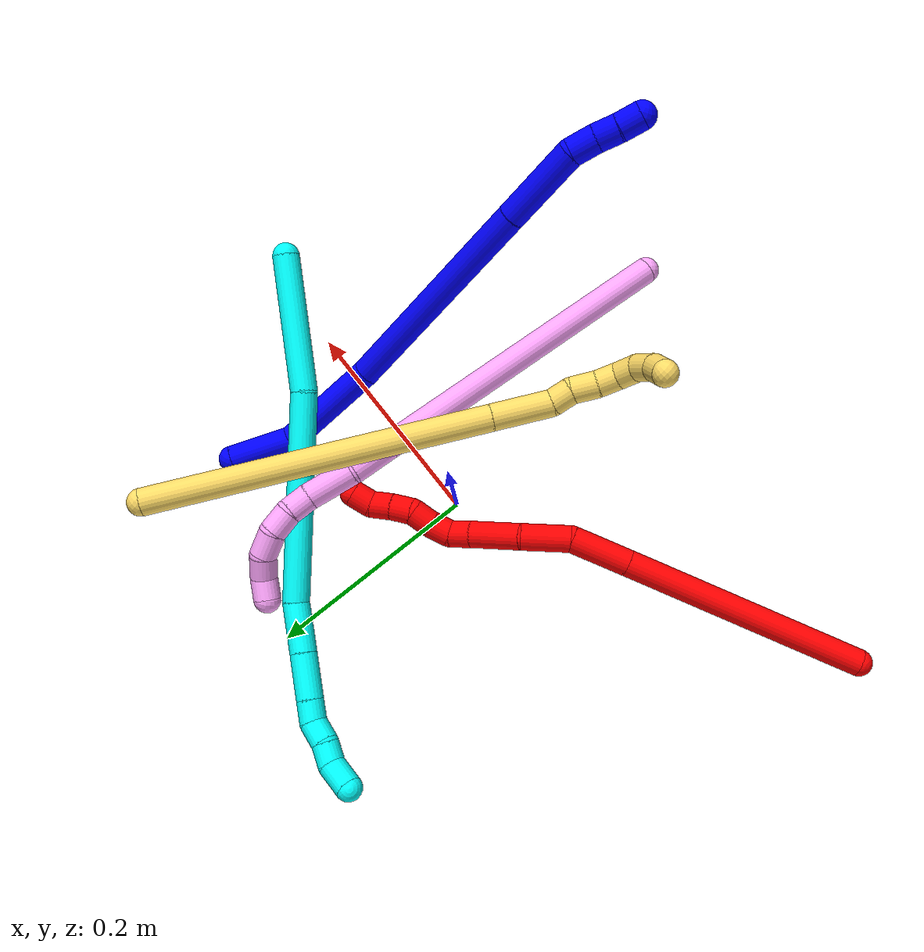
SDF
<sdf version="1.7">
 <world name="default">
  <plugin name="TubeGeneratorPlugin" filename="libtube_generator_plugin.so"/>
  <model name="photoneo_s_sensor">
   <static>1</static>
   <pose>0 0 2 1.57079 1.57079 3.14159</pose>
   <link name="link">
    <inertial><mass>0.1</mass></inertial>
    <sensor name="sensor" type="depth">
     <update_rate>30</update_rate>
     <camera>
      <horizontal_fov>1.22</horizontal_fov>
      <image><width>1920</width><height>1200</height><format>B8G8R8</format></image>
      <clip><near>0.1</near><far>4</far></clip>
      <depth_camera><output>points</output></depth_camera>
     </camera>
     <plugin name="camera_plugin" filename="libgazebo_ros_depth_camera.so">
      <baseline>0.2</baseline>
      <alwaysOn>1</alwaysOn>
      <updateRate>0.0</updateRate>
      <cameraName>camera_ir</cameraName>
      <imageTopicName>/camera/color/image_raw</imageTopicName>
      <cameraInfoTopicName>/camera/color/camera_info</cameraInfoTopicName>
      <depthImageTopicName>/camera/depth/image_raw</depthImageTopicName>
      <depthImageCameraInfoTopicName>/camera/depth/camera_info</depthImageCameraInfoTopicName>
      <pointCloudTopicName>/camera/depth/points</pointCloudTopicName>
      <frameName>fr_optical</frameName>
      <pointCloudCutoff>0.1</pointCloudCutoff>
      <pointCloudCutoffMax>2.0</pointCloudCutoffMax>
      <distortionK1>0</distortionK1>
      <distortionK2>0</distortionK2>
      <distortionK3>0</distortionK3>
      <distortionT1>0</distortionT1>
      <distortionT2>0</distortionT2>
      <CxPrime>0</CxPrime>
      <Cx>0</Cx>
      <Cy>0</Cy>
      <focalLength>0</focalLength>
      <hackBaseline>0</hackBaseline>
     </plugin>
    </sensor>
   </link>
  </model>
  <gravity>0 0 -9.8</gravity>
  <magnetic_field>6e-06 2.3e-05 -4.2e-05</magnetic_field>
  <atmosphere type="adiabatic"/>
  <physics name="default_physics" default="0" type="ode">
   <max_step_size>0.003</max_step_size>
   <real_time_factor>1</real_time_factor>
   <real_time_update_rate>1000</real_time_update_rate>
   <max_contacts>10000</max_contacts>
   <ode>
    <solver>
     <type>quick</type>
     <iters>100</iters>
     <sor>1.3</sor>
     <use_dynamic_moi_rescaling>0</use_dynamic_moi_rescaling>
    </solver>
    <constraints>
     <contact_max_correcting_vel>0</contact_max_correcting_vel>
     <contact_surface_layer>0.001</contact_surface_layer>
     <cfm>0</cfm>
     <erp>0.2</erp>
    </constraints>
   </ode>
  </physics>
  <scene><ambient>0.4 0.4 0.4 1</ambient><background>0.7 0.7 0.7 1</background><shadows>0</shadows></scene>
  <audio><device>default</device></audio>
  <spherical_coordinates>
   <surface_model>EARTH_WGS84</surface_model>
   <latitude_deg>0</latitude_deg>
   <longitude_deg>0</longitude_deg>
   <elevation>0</elevation>
   <heading_deg>0</heading_deg>
  </spherical_coordinates>
  <model name="bin">
   <static>1</static>
   <link name="bottom">
    <collision name="collision-bottom">
     <pose>0 0 -0.01 0 -0 0</pose>
     <geometry><box><size>0.8 0.6 0.02</size></box></geometry>
     <surface>
      <friction><ode><mu>100</mu><mu2>100</mu2></ode></friction>
      <contact><collide_bitmask>65535</collide_bitmask></contact>
     </surface>
    </collision>
   </link>
   <link name="west_wall">
    <collision name="collision-west_wall">
     <pose>-0.41 0 0.1 0 -0 0</pose>
     <geometry><box><size>0.02 0.6 0.2</size></box></geometry>
     <surface>
      <friction><ode><mu>100</mu><mu2>100</mu2></ode></friction>
      <contact><collide_bitmask>65535</collide_bitmask></contact>
     </surface>
    </collision>
   </link>
   <link name="east_wall">
    <collision name="collision-east_wall">
     <pose>0.41 0 0.1 0 -0 0</pose>
     <geometry><box><size>0.02 0.6 0.2</size></box></geometry>
     <surface>
      <friction><ode><mu>100</mu><mu2>100</mu2></ode></friction>
      <contact><collide_bitmask>65535</collide_bitmask></contact>
     </surface>
    </collision>
   </link>
   <link name="south_wall">
    <collision name="collision-south_wall">
     <pose>0 -0.31 0.1 0 -0 0</pose>
     <geometry><box><size>0.8 0.02 0.2</size></box></geometry>
     <surface>
      <friction><ode><mu>100</mu><mu2>100</mu2></ode></friction>
      <contact><collide_bitmask>65535</collide_bitmask></contact>
     </surface>
    </collision>
   </link>
   <link name="north_wall">
    <collision name="collision-north_wall">
     <pose>0 0.31 0.1 0 -0 0</pose>
     <geometry><box><size>0.8 0.02 0.2</size></box></geometry>
     <surface>
      <friction><ode><mu>100</mu><mu2>100</mu2></ode></friction>
      <contact><collide_bitmask>65535</collide_bitmask></contact>
     </surface>
    </collision>
   </link>
  </model>
  <model name="1">
   <static>0</static>
   <link name="1">
    <collision name="collision-cylinder-e_1_1_4">
     <pose>0.007695 -0.022865 0.015884 0.963631 0.269656 0.141632</pose>
     <geometry><cylinder><radius>0.0125</radius><length>0.057769</length></cylinder></geometry>
     <surface>
      <friction><ode><mu>1.16</mu><mu2>1.16</mu2><slip1>0</slip1><slip2>0</slip2></ode></friction>
      <contact><ode><kp>1e+06</kp><kd>1</kd><max_vel>0</max_vel><min_depth>0.001</min_depth></ode></contact>
     </surface>
    </collision>
    <visual name="visual-cylinder-e_1_1_4">
     <pose>0.007695 -0.022865 0.015884 0.963631 0.269656 0.141632</pose>
     <geometry><cylinder><radius>0.0125</radius><length>0.057769</length></cylinder></geometry>
     <material><ambient>0 0 1 1</ambient></material>
    </visual>
    <collision name="collision-cylinder-e_2_4_5">
     <pose>0.019196 -0.069936 0.074105 0.519403 0.077895 0.020707</pose>
     <geometry><cylinder><radius>0.0125</radius><length>0.097832</length></cylinder></geometry>
     <surface>
      <friction><ode><mu>1.16</mu><mu2>1.16</mu2><slip1>0</slip1><slip2>0</slip2></ode></friction>
      <contact><ode><kp>1e+06</kp><kd>1</kd><max_vel>0</max_vel><min_depth>0.001</min_depth></ode></contact>
     </surface>
    </collision>
    <visual name="visual-cylinder-e_2_4_5">
     <pose>0.019196 -0.069936 0.074105 0.519403 0.077895 0.020707</pose>
     <geometry><cylinder><radius>0.0125</radius><length>0.097832</length></cylinder></geometry>
     <material><ambient>0 0 1 1</ambient></material>
    </visual>
    <collision name="collision-cylinder-e_3_5_6">
     <pose>0.010165 -0.135884 0.209237 0.4227 -0.125498 -0.02696</pose>
     <geometry><cylinder><radius>0.0125</radius><length>0.205118</length></cylinder></geometry>
     <surface>
      <friction><ode><mu>1.16</mu><mu2>1.16</mu2><slip1>0</slip1><slip2>0</slip2></ode></friction>
      <contact><ode><kp>1e+06</kp><kd>1</kd><max_vel>0</max_vel><min_depth>0.001</min_depth></ode></contact>
     </surface>
    </collision>
    <visual name="visual-cylinder-e_3_5_6">
     <pose>0.010165 -0.135884 0.209237 0.4227 -0.125498 -0.02696</pose>
     <geometry><cylinder><radius>0.0125</radius><length>0.205118</length></cylinder></geometry>
     <material><ambient>0 0 1 1</ambient></material>
    </visual>
    <collision name="collision-cylinder-e_4_6_7">
     <pose>-0.006072 -0.192832 0.335743 0.423791 -0.091681 -0.019736</pose>
     <geometry><cylinder><radius>0.0125</radius><length>0.074273</length></cylinder></geometry>
     <surface>
      <friction><ode><mu>1.16</mu><mu2>1.16</mu2><slip1>0</slip1><slip2>0</slip2></ode></friction>
      <contact><ode><kp>1e+06</kp><kd>1</kd><max_vel>0</max_vel><min_depth>0.001</min_depth></ode></contact>
     </surface>
    </collision>
    <visual name="visual-cylinder-e_4_6_7">
     <pose>-0.006072 -0.192832 0.335743 0.423791 -0.091681 -0.019736</pose>
     <geometry><cylinder><radius>0.0125</radius><length>0.074273</length></cylinder></geometry>
     <material><ambient>0 0 1 1</ambient></material>
    </visual>
    <collision name="collision-cylinder-e_5_7_8">
     <pose>-0.008473 -0.21608 0.378211 0.742645 0.08376 0.032631</pose>
     <geometry><cylinder><radius>0.0125</radius><length>0.023864</length></cylinder></geometry>
     <surface>
      <friction><ode><mu>1.16</mu><mu2>1.16</mu2><slip1>0</slip1><slip2>0</slip2></ode></friction>
      <contact><ode><kp>1e+06</kp><kd>1</kd><max_vel>0</max_vel><min_depth>0.001</min_depth></ode></contact>
     </surface>
    </collision>
    <visual name="visual-cylinder-e_5_7_8">
     <pose>-0.008473 -0.21608 0.378211 0.742645 0.08376 0.032631</pose>
     <geometry><cylinder><radius>0.0125</radius><length>0.023864</length></cylinder></geometry>
     <material><ambient>0 0 1 1</ambient></material>
    </visual>
    <collision name="collision-cylinder-e_6_8_9">
     <pose>-0.007553 -0.231607 0.393879 0.825556 -0.007621 -0.003338</pose>
     <geometry><cylinder><radius>0.0125</radius><length>0.020375</length></cylinder></geometry>
     <surface>
      <friction><ode><mu>1.16</mu><mu2>1.16</mu2><slip1>0</slip1><slip2>0</slip2></ode></friction>
      <contact><ode><kp>1e+06</kp><kd>1</kd><max_vel>0</max_vel><min_depth>0.001</min_depth></ode></contact>
     </surface>
    </collision>
    <visual name="visual-cylinder-e_6_8_9">
     <pose>-0.007553 -0.231607 0.393879 0.825556 -0.007621 -0.003338</pose>
     <geometry><cylinder><radius>0.0125</radius><length>0.020375</length></cylinder></geometry>
     <material><ambient>0 0 1 1</ambient></material>
    </visual>
    <collision name="collision-cylinder-e_7_9_2">
     <pose>-0.006916 -0.246134 0.408387 0.747185 0.068893 0.027015</pose>
     <geometry><cylinder><radius>0.0125</radius><length>0.020769</length></cylinder></geometry>
     <surface>
      <friction><ode><mu>1.16</mu><mu2>1.16</mu2><slip1>0</slip1><slip2>0</slip2></ode></friction>
      <contact><ode><kp>1e+06</kp><kd>1</kd><max_vel>0</max_vel><min_depth>0.001</min_depth></ode></contact>
     </surface>
    </collision>
    <visual name="visual-cylinder-e_7_9_2">
     <pose>-0.006916 -0.246134 0.408387 0.747185 0.068893 0.027015</pose>
     <geometry><cylinder><radius>0.0125</radius><length>0.020769</length></cylinder></geometry>
     <material><ambient>0 0 1 1</ambient></material>
    </visual>
    <collision name="collision-sphere-2">
     <pose>-0.006201 -0.253175 0.415987 0 -0 0</pose>
     <geometry><sphere><radius>0.0125</radius></sphere></geometry>
     <surface>
      <friction><ode><mu>1.16</mu><mu2>1.16</mu2><slip1>0</slip1><slip2>0</slip2></ode></friction>
      <contact><ode><kp>1e+06</kp><kd>1</kd><max_vel>0</max_vel><min_depth>0.001</min_depth></ode></contact>
     </surface>
    </collision>
    <visual name="visual-sphere-2">
     <pose>-0.006201 -0.253175 0.415987 0 -0 0</pose>
     <geometry><sphere><radius>0.0125</radius></sphere></geometry>
     <material><ambient>0 0 1 1</ambient></material>
    </visual>
    <collision name="collision-sphere-9">
     <pose>-0.007631 -0.239094 0.400787 0 -0 0</pose>
     <geometry><sphere><radius>0.0125</radius></sphere></geometry>
     <surface>
      <friction><ode><mu>1.16</mu><mu2>1.16</mu2><slip1>0</slip1><slip2>0</slip2></ode></friction>
      <contact><ode><kp>1e+06</kp><kd>1</kd><max_vel>0</max_vel><min_depth>0.001</min_depth></ode></contact>
     </surface>
    </collision>
    <visual name="visual-sphere-9">
     <pose>-0.007631 -0.239094 0.400787 0 -0 0</pose>
     <geometry><sphere><radius>0.0125</radius></sphere></geometry>
     <material><ambient>0 0 1 1</ambient></material>
    </visual>
    <collision name="collision-sphere-4">
     <pose>0.01539 -0.045729 0.031769 0 -0 0</pose>
     <geometry><sphere><radius>0.0125</radius></sphere></geometry>
     <surface>
      <friction><ode><mu>1.16</mu><mu2>1.16</mu2><slip1>0</slip1><slip2>0</slip2></ode></friction>
      <contact><ode><kp>1e+06</kp><kd>1</kd><max_vel>0</max_vel><min_depth>0.001</min_depth></ode></contact>
     </surface>
    </collision>
    <visual name="visual-sphere-4">
     <pose>0.01539 -0.045729 0.031769 0 -0 0</pose>
     <geometry><sphere><radius>0.0125</radius></sphere></geometry>
     <material><ambient>0 0 1 1</ambient></material>
    </visual>
    <collision name="collision-sphere-1">
     <geometry><sphere><radius>0.0125</radius></sphere></geometry>
     <surface>
      <friction><ode><mu>1.16</mu><mu2>1.16</mu2><slip1>0</slip1><slip2>0</slip2></ode></friction>
      <contact><ode><kp>1e+06</kp><kd>1</kd><max_vel>0</max_vel><min_depth>0.001</min_depth></ode></contact>
     </surface>
    </collision>
    <visual name="visual-sphere-1">
     <geometry><sphere><radius>0.0125</radius></sphere></geometry>
     <material><ambient>0 0 1 1</ambient></material>
    </visual>
    <collision name="collision-sphere-8">
     <pose>-0.007475 -0.22412 0.38697 0 -0 0</pose>
     <geometry><sphere><radius>0.0125</radius></sphere></geometry>
     <surface>
      <friction><ode><mu>1.16</mu><mu2>1.16</mu2><slip1>0</slip1><slip2>0</slip2></ode></friction>
      <contact><ode><kp>1e+06</kp><kd>1</kd><max_vel>0</max_vel><min_depth>0.001</min_depth></ode></contact>
     </surface>
    </collision>
    <visual name="visual-sphere-8">
     <pose>-0.007475 -0.22412 0.38697 0 -0 0</pose>
     <geometry><sphere><radius>0.0125</radius></sphere></geometry>
     <material><ambient>0 0 1 1</ambient></material>
    </visual>
    <collision name="collision-sphere-5">
     <pose>0.023003 -0.094142 0.116441 0 -0 0</pose>
     <geometry><sphere><radius>0.0125</radius></sphere></geometry>
     <surface>
      <friction><ode><mu>1.16</mu><mu2>1.16</mu2><slip1>0</slip1><slip2>0</slip2></ode></friction>
      <contact><ode><kp>1e+06</kp><kd>1</kd><max_vel>0</max_vel><min_depth>0.001</min_depth></ode></contact>
     </surface>
    </collision>
    <visual name="visual-sphere-5">
     <pose>0.023003 -0.094142 0.116441 0 -0 0</pose>
     <geometry><sphere><radius>0.0125</radius></sphere></geometry>
     <material><ambient>0 0 1 1</ambient></material>
    </visual>
    <collision name="collision-sphere-6">
     <pose>-0.002672 -0.177625 0.302034 0 -0 0</pose>
     <geometry><sphere><radius>0.0125</radius></sphere></geometry>
     <surface>
      <friction><ode><mu>1.16</mu><mu2>1.16</mu2><slip1>0</slip1><slip2>0</slip2></ode></friction>
      <contact><ode><kp>1e+06</kp><kd>1</kd><max_vel>0</max_vel><min_depth>0.001</min_depth></ode></contact>
     </surface>
    </collision>
    <visual name="visual-sphere-6">
     <pose>-0.002672 -0.177625 0.302034 0 -0 0</pose>
     <geometry><sphere><radius>0.0125</radius></sphere></geometry>
     <material><ambient>0 0 1 1</ambient></material>
    </visual>
    <collision name="collision-sphere-7">
     <pose>-0.009472 -0.208039 0.369452 0 -0 0</pose>
     <geometry><sphere><radius>0.0125</radius></sphere></geometry>
     <surface>
      <friction><ode><mu>1.16</mu><mu2>1.16</mu2><slip1>0</slip1><slip2>0</slip2></ode></friction>
      <contact><ode><kp>1e+06</kp><kd>1</kd><max_vel>0</max_vel><min_depth>0.001</min_depth></ode></contact>
     </surface>
    </collision>
    <visual name="visual-sphere-7">
     <pose>-0.009472 -0.208039 0.369452 0 -0 0</pose>
     <geometry><sphere><radius>0.0125</radius></sphere></geometry>
     <material><ambient>0 0 1 1</ambient></material>
    </visual>
    <inertial>
     <pose>0.006914 -0.130689 0.20311 0 -0 0</pose>
     <mass>0.5</mass>
     <inertia>
      <ixx>0.000846</ixx>
      <ixy>0</ixy>
      <ixz>0</ixz>
      <iyy>0.000748</iyy>
      <iyz>0</iyz>
      <izz>0.000485</izz>
     </inertia>
    </inertial>
   </link>
   <pose>0.163742 0.138678 0.011489 0.1332 1.02609 -0.883614</pose>
  </model>
  <model name="2">
   <static>0</static>
   <link name="2">
    <collision name="collision-cylinder-e_1_1_4">
     <pose>0.070626 -0.000275 -0.09063 3.13856 0.66197 3.13278</pose>
     <geometry><cylinder><radius>0.0125</radius><length>0.229799</length></cylinder></geometry>
     <surface>
      <friction><ode><mu>1.16</mu><mu2>1.16</mu2><slip1>0</slip1><slip2>0</slip2></ode></friction>
      <contact><ode><kp>1e+06</kp><kd>1</kd><max_vel>0</max_vel><min_depth>0.001</min_depth></ode></contact>
     </surface>
    </collision>
    <visual name="visual-cylinder-e_1_1_4">
     <pose>0.070626 -0.000275 -0.09063 3.13856 0.66197 3.13278</pose>
     <geometry><cylinder><radius>0.0125</radius><length>0.229799</length></cylinder></geometry>
     <material><ambient>1 0 0 1</ambient></material>
    </visual>
    <collision name="collision-cylinder-e_2_4_5">
     <pose>0.158697 -0.000529 -0.203004 -3.14068 0.67618 -3.13899</pose>
     <geometry><cylinder><radius>0.0125</radius><length>0.055754</length></cylinder></geometry>
     <surface>
      <friction><ode><mu>1.16</mu><mu2>1.16</mu2><slip1>0</slip1><slip2>0</slip2></ode></friction>
      <contact><ode><kp>1e+06</kp><kd>1</kd><max_vel>0</max_vel><min_depth>0.001</min_depth></ode></contact>
     </surface>
    </collision>
    <visual name="visual-cylinder-e_2_4_5">
     <pose>0.158697 -0.000529 -0.203004 -3.14068 0.67618 -3.13899</pose>
     <geometry><cylinder><radius>0.0125</radius><length>0.055754</length></cylinder></geometry>
     <material><ambient>1 0 0 1</ambient></material>
    </visual>
    <collision name="collision-cylinder-e_3_5_6">
     <pose>0.188216 0.007845 -0.242435 -2.70031 0.552927 -1.80373</pose>
     <geometry><cylinder><radius>0.0125</radius><length>0.045974</length></cylinder></geometry>
     <surface>
      <friction><ode><mu>1.16</mu><mu2>1.16</mu2><slip1>0</slip1><slip2>0</slip2></ode></friction>
      <contact><ode><kp>1e+06</kp><kd>1</kd><max_vel>0</max_vel><min_depth>0.001</min_depth></ode></contact>
     </surface>
    </collision>
    <visual name="visual-cylinder-e_3_5_6">
     <pose>0.188216 0.007845 -0.242435 -2.70031 0.552927 -1.80373</pose>
     <geometry><cylinder><radius>0.0125</radius><length>0.045974</length></cylinder></geometry>
     <material><ambient>1 0 0 1</ambient></material>
    </visual>
    <collision name="collision-cylinder-e_4_6_7">
     <pose>0.207964 0.025138 -0.280882 -2.73503 0.32742 -1.35118</pose>
     <geometry><cylinder><radius>0.0125</radius><length>0.047737</length></cylinder></geometry>
     <surface>
      <friction><ode><mu>1.16</mu><mu2>1.16</mu2><slip1>0</slip1><slip2>0</slip2></ode></friction>
      <contact><ode><kp>1e+06</kp><kd>1</kd><max_vel>0</max_vel><min_depth>0.001</min_depth></ode></contact>
     </surface>
    </collision>
    <visual name="visual-cylinder-e_4_6_7">
     <pose>0.207964 0.025138 -0.280882 -2.73503 0.32742 -1.35118</pose>
     <geometry><cylinder><radius>0.0125</radius><length>0.047737</length></cylinder></geometry>
     <material><ambient>1 0 0 1</ambient></material>
    </visual>
    <collision name="collision-cylinder-e_5_7_8">
     <pose>0.219845 0.038069 -0.309854 -2.68902 0.431453 -1.52143</pose>
     <geometry><cylinder><radius>0.0125</radius><length>0.02011</length></cylinder></geometry>
     <surface>
      <friction><ode><mu>1.16</mu><mu2>1.16</mu2><slip1>0</slip1><slip2>0</slip2></ode></friction>
      <contact><ode><kp>1e+06</kp><kd>1</kd><max_vel>0</max_vel><min_depth>0.001</min_depth></ode></contact>
     </surface>
    </collision>
    <visual name="visual-cylinder-e_5_7_8">
     <pose>0.219845 0.038069 -0.309854 -2.68902 0.431453 -1.52143</pose>
     <geometry><cylinder><radius>0.0125</radius><length>0.02011</length></cylinder></geometry>
     <material><ambient>1 0 0 1</ambient></material>
    </visual>
    <collision name="collision-cylinder-e_6_8_9">
     <pose>0.229747 0.04158 -0.326336 3.08324 0.602531 2.95428</pose>
     <geometry><cylinder><radius>0.0125</radius><length>0.020104</length></cylinder></geometry>
     <surface>
      <friction><ode><mu>1.16</mu><mu2>1.16</mu2><slip1>0</slip1><slip2>0</slip2></ode></friction>
      <contact><ode><kp>1e+06</kp><kd>1</kd><max_vel>0</max_vel><min_depth>0.001</min_depth></ode></contact>
     </surface>
    </collision>
    <visual name="visual-cylinder-e_6_8_9">
     <pose>0.229747 0.04158 -0.326336 3.08324 0.602531 2.95428</pose>
     <geometry><cylinder><radius>0.0125</radius><length>0.020104</length></cylinder></geometry>
     <material><ambient>1 0 0 1</ambient></material>
    </visual>
    <collision name="collision-cylinder-e_7_9_10">
     <pose>0.241837 0.038913 -0.342268 2.86402 0.67609 2.38516</pose>
     <geometry><cylinder><radius>0.0125</radius><length>0.020433</length></cylinder></geometry>
     <surface>
      <friction><ode><mu>1.16</mu><mu2>1.16</mu2><slip1>0</slip1><slip2>0</slip2></ode></friction>
      <contact><ode><kp>1e+06</kp><kd>1</kd><max_vel>0</max_vel><min_depth>0.001</min_depth></ode></contact>
     </surface>
    </collision>
    <visual name="visual-cylinder-e_7_9_10">
     <pose>0.241837 0.038913 -0.342268 2.86402 0.67609 2.38516</pose>
     <geometry><cylinder><radius>0.0125</radius><length>0.020433</length></cylinder></geometry>
     <material><ambient>1 0 0 1</ambient></material>
    </visual>
    <collision name="collision-cylinder-e_8_10_11">
     <pose>0.252475 0.038766 -0.358791 -2.91566 0.436941 -2.19677</pose>
     <geometry><cylinder><radius>0.0125</radius><length>0.020065</length></cylinder></geometry>
     <surface>
      <friction><ode><mu>1.16</mu><mu2>1.16</mu2><slip1>0</slip1><slip2>0</slip2></ode></friction>
      <contact><ode><kp>1e+06</kp><kd>1</kd><max_vel>0</max_vel><min_depth>0.001</min_depth></ode></contact>
     </surface>
    </collision>
    <visual name="visual-cylinder-e_8_10_11">
     <pose>0.252475 0.038766 -0.358791 -2.91566 0.436941 -2.19677</pose>
     <geometry><cylinder><radius>0.0125</radius><length>0.020065</length></cylinder></geometry>
     <material><ambient>1 0 0 1</ambient></material>
    </visual>
    <collision name="collision-cylinder-e_9_11_12">
     <pose>0.26147 0.043788 -0.375937 -2.79582 0.494563 -1.93125</pose>
     <geometry><cylinder><radius>0.0125</radius><length>0.020015</length></cylinder></geometry>
     <surface>
      <friction><ode><mu>1.16</mu><mu2>1.16</mu2><slip1>0</slip1><slip2>0</slip2></ode></friction>
      <contact><ode><kp>1e+06</kp><kd>1</kd><max_vel>0</max_vel><min_depth>0.001</min_depth></ode></contact>
     </surface>
    </collision>
    <visual name="visual-cylinder-e_9_11_12">
     <pose>0.26147 0.043788 -0.375937 -2.79582 0.494563 -1.93125</pose>
     <geometry><cylinder><radius>0.0125</radius><length>0.020015</length></cylinder></geometry>
     <material><ambient>1 0 0 1</ambient></material>
    </visual>
    <collision name="collision-cylinder-e_10_12_2">
     <pose>0.272372 0.045382 -0.391989 2.9643 0.662298 2.63565</pose>
     <geometry><cylinder><radius>0.0125</radius><length>0.020008</length></cylinder></geometry>
     <surface>
      <friction><ode><mu>1.16</mu><mu2>1.16</mu2><slip1>0</slip1><slip2>0</slip2></ode></friction>
      <contact><ode><kp>1e+06</kp><kd>1</kd><max_vel>0</max_vel><min_depth>0.001</min_depth></ode></contact>
     </surface>
    </collision>
    <visual name="visual-cylinder-e_10_12_2">
     <pose>0.272372 0.045382 -0.391989 2.9643 0.662298 2.63565</pose>
     <geometry><cylinder><radius>0.0125</radius><length>0.020008</length></cylinder></geometry>
     <material><ambient>1 0 0 1</ambient></material>
    </visual>
    <collision name="collision-sphere-2">
     <pose>0.278524 0.04399 -0.399754 0 -0 0</pose>
     <geometry><sphere><radius>0.0125</radius></sphere></geometry>
     <surface>
      <friction><ode><mu>1.16</mu><mu2>1.16</mu2><slip1>0</slip1><slip2>0</slip2></ode></friction>
      <contact><ode><kp>1e+06</kp><kd>1</kd><max_vel>0</max_vel><min_depth>0.001</min_depth></ode></contact>
     </surface>
    </collision>
    <visual name="visual-sphere-2">
     <pose>0.278524 0.04399 -0.399754 0 -0 0</pose>
     <geometry><sphere><radius>0.0125</radius></sphere></geometry>
     <material><ambient>1 0 0 1</ambient></material>
    </visual>
    <collision name="collision-sphere-12">
     <pose>0.26622 0.046773 -0.384224 0 -0 0</pose>
     <geometry><sphere><radius>0.0125</radius></sphere></geometry>
     <surface>
      <friction><ode><mu>1.16</mu><mu2>1.16</mu2><slip1>0</slip1><slip2>0</slip2></ode></friction>
      <contact><ode><kp>1e+06</kp><kd>1</kd><max_vel>0</max_vel><min_depth>0.001</min_depth></ode></contact>
     </surface>
    </collision>
    <visual name="visual-sphere-12">
     <pose>0.26622 0.046773 -0.384224 0 -0 0</pose>
     <geometry><sphere><radius>0.0125</radius></sphere></geometry>
     <material><ambient>1 0 0 1</ambient></material>
    </visual>
    <collision name="collision-sphere-11">
     <pose>0.25672 0.040802 -0.36765 0 -0 0</pose>
     <geometry><sphere><radius>0.0125</radius></sphere></geometry>
     <surface>
      <friction><ode><mu>1.16</mu><mu2>1.16</mu2><slip1>0</slip1><slip2>0</slip2></ode></friction>
      <contact><ode><kp>1e+06</kp><kd>1</kd><max_vel>0</max_vel><min_depth>0.001</min_depth></ode></contact>
     </surface>
    </collision>
    <visual name="visual-sphere-11">
     <pose>0.25672 0.040802 -0.36765 0 -0 0</pose>
     <geometry><sphere><radius>0.0125</radius></sphere></geometry>
     <material><ambient>1 0 0 1</ambient></material>
    </visual>
    <collision name="collision-sphere-10">
     <pose>0.24823 0.03673 -0.349932 0 -0 0</pose>
     <geometry><sphere><radius>0.0125</radius></sphere></geometry>
     <surface>
      <friction><ode><mu>1.16</mu><mu2>1.16</mu2><slip1>0</slip1><slip2>0</slip2></ode></friction>
      <contact><ode><kp>1e+06</kp><kd>1</kd><max_vel>0</max_vel><min_depth>0.001</min_depth></ode></contact>
     </surface>
    </collision>
    <visual name="visual-sphere-10">
     <pose>0.24823 0.03673 -0.349932 0 -0 0</pose>
     <geometry><sphere><radius>0.0125</radius></sphere></geometry>
     <material><ambient>1 0 0 1</ambient></material>
    </visual>
    <collision name="collision-sphere-9">
     <pose>0.235444 0.041097 -0.334604 0 -0 0</pose>
     <geometry><sphere><radius>0.0125</radius></sphere></geometry>
     <surface>
      <friction><ode><mu>1.16</mu><mu2>1.16</mu2><slip1>0</slip1><slip2>0</slip2></ode></friction>
      <contact><ode><kp>1e+06</kp><kd>1</kd><max_vel>0</max_vel><min_depth>0.001</min_depth></ode></contact>
     </surface>
    </collision>
    <visual name="visual-sphere-9">
     <pose>0.235444 0.041097 -0.334604 0 -0 0</pose>
     <geometry><sphere><radius>0.0125</radius></sphere></geometry>
     <material><ambient>1 0 0 1</ambient></material>
    </visual>
    <collision name="collision-sphere-4">
     <pose>0.141251 -0.000549 -0.181261 0 -0 0</pose>
     <geometry><sphere><radius>0.0125</radius></sphere></geometry>
     <surface>
      <friction><ode><mu>1.16</mu><mu2>1.16</mu2><slip1>0</slip1><slip2>0</slip2></ode></friction>
      <contact><ode><kp>1e+06</kp><kd>1</kd><max_vel>0</max_vel><min_depth>0.001</min_depth></ode></contact>
     </surface>
    </collision>
    <visual name="visual-sphere-4">
     <pose>0.141251 -0.000549 -0.181261 0 -0 0</pose>
     <geometry><sphere><radius>0.0125</radius></sphere></geometry>
     <material><ambient>1 0 0 1</ambient></material>
    </visual>
    <collision name="collision-sphere-1">
     <geometry><sphere><radius>0.0125</radius></sphere></geometry>
     <surface>
      <friction><ode><mu>1.16</mu><mu2>1.16</mu2><slip1>0</slip1><slip2>0</slip2></ode></friction>
      <contact><ode><kp>1e+06</kp><kd>1</kd><max_vel>0</max_vel><min_depth>0.001</min_depth></ode></contact>
     </surface>
    </collision>
    <visual name="visual-sphere-1">
     <geometry><sphere><radius>0.0125</radius></sphere></geometry>
     <material><ambient>1 0 0 1</ambient></material>
    </visual>
    <collision name="collision-sphere-8">
     <pose>0.22405 0.042063 -0.318068 0 -0 0</pose>
     <geometry><sphere><radius>0.0125</radius></sphere></geometry>
     <surface>
      <friction><ode><mu>1.16</mu><mu2>1.16</mu2><slip1>0</slip1><slip2>0</slip2></ode></friction>
      <contact><ode><kp>1e+06</kp><kd>1</kd><max_vel>0</max_vel><min_depth>0.001</min_depth></ode></contact>
     </surface>
    </collision>
    <visual name="visual-sphere-8">
     <pose>0.22405 0.042063 -0.318068 0 -0 0</pose>
     <geometry><sphere><radius>0.0125</radius></sphere></geometry>
     <material><ambient>1 0 0 1</ambient></material>
    </visual>
    <collision name="collision-sphere-5">
     <pose>0.176143 -0.000509 -0.224747 0 -0 0</pose>
     <geometry><sphere><radius>0.0125</radius></sphere></geometry>
     <surface>
      <friction><ode><mu>1.16</mu><mu2>1.16</mu2><slip1>0</slip1><slip2>0</slip2></ode></friction>
      <contact><ode><kp>1e+06</kp><kd>1</kd><max_vel>0</max_vel><min_depth>0.001</min_depth></ode></contact>
     </surface>
    </collision>
    <visual name="visual-sphere-5">
     <pose>0.176143 -0.000509 -0.224747 0 -0 0</pose>
     <geometry><sphere><radius>0.0125</radius></sphere></geometry>
     <material><ambient>1 0 0 1</ambient></material>
    </visual>
    <collision name="collision-sphere-6">
     <pose>0.200288 0.0162 -0.260123 0 -0 0</pose>
     <geometry><sphere><radius>0.0125</radius></sphere></geometry>
     <surface>
      <friction><ode><mu>1.16</mu><mu2>1.16</mu2><slip1>0</slip1><slip2>0</slip2></ode></friction>
      <contact><ode><kp>1e+06</kp><kd>1</kd><max_vel>0</max_vel><min_depth>0.001</min_depth></ode></contact>
     </surface>
    </collision>
    <visual name="visual-sphere-6">
     <pose>0.200288 0.0162 -0.260123 0 -0 0</pose>
     <geometry><sphere><radius>0.0125</radius></sphere></geometry>
     <material><ambient>1 0 0 1</ambient></material>
    </visual>
    <collision name="collision-sphere-7">
     <pose>0.21564 0.034075 -0.30164 0 -0 0</pose>
     <geometry><sphere><radius>0.0125</radius></sphere></geometry>
     <surface>
      <friction><ode><mu>1.16</mu><mu2>1.16</mu2><slip1>0</slip1><slip2>0</slip2></ode></friction>
      <contact><ode><kp>1e+06</kp><kd>1</kd><max_vel>0</max_vel><min_depth>0.001</min_depth></ode></contact>
     </surface>
    </collision>
    <visual name="visual-sphere-7">
     <pose>0.21564 0.034075 -0.30164 0 -0 0</pose>
     <geometry><sphere><radius>0.0125</radius></sphere></geometry>
     <material><ambient>1 0 0 1</ambient></material>
    </visual>
    <inertial>
     <pose>0.146777 0.012854 -0.198102 0 -0 0</pose>
     <mass>0.5</mass>
     <inertia>
      <ixx>-0.000813</ixx>
      <ixy>0</ixy>
      <ixz>0</ixz>
      <iyy>0.001036</iyy>
      <iyz>0</iyz>
      <izz>-0.000688</izz>
     </inertia>
    </inertial>
   </link>
   <pose>-0.343179 -0.196593 0.011497 -0.415401 -0.948417 0.825891</pose>
  </model>
  <model name="3">
   <static>0</static>
   <link name="3">
    <collision name="collision-cylinder-e_1_1_4">
     <pose>-0.057282 0.027238 0.0049 -1.39279 -1.12073 0.966336</pose>
     <geometry><cylinder><radius>0.0125</radius><length>0.127234</length></cylinder></geometry>
     <surface>
      <friction><ode><mu>1.16</mu><mu2>1.16</mu2><slip1>0</slip1><slip2>0</slip2></ode></friction>
      <contact><ode><kp>1e+06</kp><kd>1</kd><max_vel>0</max_vel><min_depth>0.001</min_depth></ode></contact>
     </surface>
    </collision>
    <visual name="visual-cylinder-e_1_1_4">
     <pose>-0.057282 0.027238 0.0049 -1.39279 -1.12073 0.966336</pose>
     <geometry><cylinder><radius>0.0125</radius><length>0.127234</length></cylinder></geometry>
     <material><ambient>0.003922 1 0.996078 1</ambient></material>
    </visual>
    <collision name="collision-cylinder-e_2_4_5">
     <pose>-0.205463 0.080382 0.029146 -0.929389 -1.22905 0.680045</pose>
     <geometry><cylinder><radius>0.0125</radius><length>0.192956</length></cylinder></geometry>
     <surface>
      <friction><ode><mu>1.16</mu><mu2>1.16</mu2><slip1>0</slip1><slip2>0</slip2></ode></friction>
      <contact><ode><kp>1e+06</kp><kd>1</kd><max_vel>0</max_vel><min_depth>0.001</min_depth></ode></contact>
     </surface>
    </collision>
    <visual name="visual-cylinder-e_2_4_5">
     <pose>-0.205463 0.080382 0.029146 -0.929389 -1.22905 0.680045</pose>
     <geometry><cylinder><radius>0.0125</radius><length>0.192956</length></cylinder></geometry>
     <material><ambient>0.003922 1 0.996078 1</ambient></material>
    </visual>
    <collision name="collision-cylinder-e_3_5_6">
     <pose>-0.317347 0.116602 0.04776 -1.64166 -1.11301 1.17759</pose>
     <geometry><cylinder><radius>0.0125</radius><length>0.046788</length></cylinder></geometry>
     <surface>
      <friction><ode><mu>1.16</mu><mu2>1.16</mu2><slip1>0</slip1><slip2>0</slip2></ode></friction>
      <contact><ode><kp>1e+06</kp><kd>1</kd><max_vel>0</max_vel><min_depth>0.001</min_depth></ode></contact>
     </surface>
    </collision>
    <visual name="visual-cylinder-e_3_5_6">
     <pose>-0.317347 0.116602 0.04776 -1.64166 -1.11301 1.17759</pose>
     <geometry><cylinder><radius>0.0125</radius><length>0.046788</length></cylinder></geometry>
     <material><ambient>0.003922 1 0.996078 1</ambient></material>
    </visual>
    <collision name="collision-cylinder-e_4_6_7">
     <pose>-0.357397 0.136161 0.046651 -1.61154 -1.11895 1.15594</pose>
     <geometry><cylinder><radius>0.0125</radius><length>0.042382</length></cylinder></geometry>
     <surface>
      <friction><ode><mu>1.16</mu><mu2>1.16</mu2><slip1>0</slip1><slip2>0</slip2></ode></friction>
      <contact><ode><kp>1e+06</kp><kd>1</kd><max_vel>0</max_vel><min_depth>0.001</min_depth></ode></contact>
     </surface>
    </collision>
    <visual name="visual-cylinder-e_4_6_7">
     <pose>-0.357397 0.136161 0.046651 -1.61154 -1.11895 1.15594</pose>
     <geometry><cylinder><radius>0.0125</radius><length>0.042382</length></cylinder></geometry>
     <material><ambient>0.003922 1 0.996078 1</ambient></material>
    </visual>
    <collision name="collision-cylinder-e_5_7_8">
     <pose>-0.385859 0.150034 0.046072 -1.61449 -1.11276 1.15234</pose>
     <geometry><cylinder><radius>0.0125</radius><length>0.020955</length></cylinder></geometry>
     <surface>
      <friction><ode><mu>1.16</mu><mu2>1.16</mu2><slip1>0</slip1><slip2>0</slip2></ode></friction>
      <contact><ode><kp>1e+06</kp><kd>1</kd><max_vel>0</max_vel><min_depth>0.001</min_depth></ode></contact>
     </surface>
    </collision>
    <visual name="visual-cylinder-e_5_7_8">
     <pose>-0.385859 0.150034 0.046072 -1.61449 -1.11276 1.15234</pose>
     <geometry><cylinder><radius>0.0125</radius><length>0.020955</length></cylinder></geometry>
     <material><ambient>0.003922 1 0.996078 1</ambient></material>
    </visual>
    <collision name="collision-cylinder-e_6_8_9">
     <pose>-0.402303 0.162367 0.041713 -2.06552 -0.677787 1.06707</pose>
     <geometry><cylinder><radius>0.0125</radius><length>0.022476</length></cylinder></geometry>
     <surface>
      <friction><ode><mu>1.16</mu><mu2>1.16</mu2><slip1>0</slip1><slip2>0</slip2></ode></friction>
      <contact><ode><kp>1e+06</kp><kd>1</kd><max_vel>0</max_vel><min_depth>0.001</min_depth></ode></contact>
     </surface>
    </collision>
    <visual name="visual-cylinder-e_6_8_9">
     <pose>-0.402303 0.162367 0.041713 -2.06552 -0.677787 1.06707</pose>
     <geometry><cylinder><radius>0.0125</radius><length>0.022476</length></cylinder></geometry>
     <material><ambient>0.003922 1 0.996078 1</ambient></material>
    </visual>
    <collision name="collision-cylinder-e_7_9_10">
     <pose>-0.417491 0.175667 0.035916 -1.85601 -0.949268 1.20267</pose>
     <geometry><cylinder><radius>0.0125</radius><length>0.020027</length></cylinder></geometry>
     <surface>
      <friction><ode><mu>1.16</mu><mu2>1.16</mu2><slip1>0</slip1><slip2>0</slip2></ode></friction>
      <contact><ode><kp>1e+06</kp><kd>1</kd><max_vel>0</max_vel><min_depth>0.001</min_depth></ode></contact>
     </surface>
    </collision>
    <visual name="visual-cylinder-e_7_9_10">
     <pose>-0.417491 0.175667 0.035916 -1.85601 -0.949268 1.20267</pose>
     <geometry><cylinder><radius>0.0125</radius><length>0.020027</length></cylinder></geometry>
     <material><ambient>0.003922 1 0.996078 1</ambient></material>
    </visual>
    <collision name="collision-cylinder-e_8_10_2">
     <pose>-0.432622 0.191103 0.028031 -2.13622 -0.54024 0.93308</pose>
     <geometry><cylinder><radius>0.0125</radius><length>0.027181</length></cylinder></geometry>
     <surface>
      <friction><ode><mu>1.16</mu><mu2>1.16</mu2><slip1>0</slip1><slip2>0</slip2></ode></friction>
      <contact><ode><kp>1e+06</kp><kd>1</kd><max_vel>0</max_vel><min_depth>0.001</min_depth></ode></contact>
     </surface>
    </collision>
    <visual name="visual-cylinder-e_8_10_2">
     <pose>-0.432622 0.191103 0.028031 -2.13622 -0.54024 0.93308</pose>
     <geometry><cylinder><radius>0.0125</radius><length>0.027181</length></cylinder></geometry>
     <material><ambient>0.003922 1 0.996078 1</ambient></material>
    </visual>
    <collision name="collision-sphere-2">
     <pose>-0.439613 0.200944 0.021786 0 -0 0</pose>
     <geometry><sphere><radius>0.0125</radius></sphere></geometry>
     <surface>
      <friction><ode><mu>1.16</mu><mu2>1.16</mu2><slip1>0</slip1><slip2>0</slip2></ode></friction>
      <contact><ode><kp>1e+06</kp><kd>1</kd><max_vel>0</max_vel><min_depth>0.001</min_depth></ode></contact>
     </surface>
    </collision>
    <visual name="visual-sphere-2">
     <pose>-0.439613 0.200944 0.021786 0 -0 0</pose>
     <geometry><sphere><radius>0.0125</radius></sphere></geometry>
     <material><ambient>0.003922 1 0.996078 1</ambient></material>
    </visual>
    <collision name="collision-sphere-10">
     <pose>-0.425632 0.181262 0.034275 0 -0 0</pose>
     <geometry><sphere><radius>0.0125</radius></sphere></geometry>
     <surface>
      <friction><ode><mu>1.16</mu><mu2>1.16</mu2><slip1>0</slip1><slip2>0</slip2></ode></friction>
      <contact><ode><kp>1e+06</kp><kd>1</kd><max_vel>0</max_vel><min_depth>0.001</min_depth></ode></contact>
     </surface>
    </collision>
    <visual name="visual-sphere-10">
     <pose>-0.425632 0.181262 0.034275 0 -0 0</pose>
     <geometry><sphere><radius>0.0125</radius></sphere></geometry>
     <material><ambient>0.003922 1 0.996078 1</ambient></material>
    </visual>
    <collision name="collision-sphere-9">
     <pose>-0.40935 0.170072 0.037557 0 -0 0</pose>
     <geometry><sphere><radius>0.0125</radius></sphere></geometry>
     <surface>
      <friction><ode><mu>1.16</mu><mu2>1.16</mu2><slip1>0</slip1><slip2>0</slip2></ode></friction>
      <contact><ode><kp>1e+06</kp><kd>1</kd><max_vel>0</max_vel><min_depth>0.001</min_depth></ode></contact>
     </surface>
    </collision>
    <visual name="visual-sphere-9">
     <pose>-0.40935 0.170072 0.037557 0 -0 0</pose>
     <geometry><sphere><radius>0.0125</radius></sphere></geometry>
     <material><ambient>0.003922 1 0.996078 1</ambient></material>
    </visual>
    <collision name="collision-sphere-4">
     <pose>-0.114564 0.054476 0.009801 0 -0 0</pose>
     <geometry><sphere><radius>0.0125</radius></sphere></geometry>
     <surface>
      <friction><ode><mu>1.16</mu><mu2>1.16</mu2><slip1>0</slip1><slip2>0</slip2></ode></friction>
      <contact><ode><kp>1e+06</kp><kd>1</kd><max_vel>0</max_vel><min_depth>0.001</min_depth></ode></contact>
     </surface>
    </collision>
    <visual name="visual-sphere-4">
     <pose>-0.114564 0.054476 0.009801 0 -0 0</pose>
     <geometry><sphere><radius>0.0125</radius></sphere></geometry>
     <material><ambient>0.003922 1 0.996078 1</ambient></material>
    </visual>
    <collision name="collision-sphere-1">
     <geometry><sphere><radius>0.0125</radius></sphere></geometry>
     <surface>
      <friction><ode><mu>1.16</mu><mu2>1.16</mu2><slip1>0</slip1><slip2>0</slip2></ode></friction>
      <contact><ode><kp>1e+06</kp><kd>1</kd><max_vel>0</max_vel><min_depth>0.001</min_depth></ode></contact>
     </surface>
    </collision>
    <visual name="visual-sphere-1">
     <geometry><sphere><radius>0.0125</radius></sphere></geometry>
     <material><ambient>0.003922 1 0.996078 1</ambient></material>
    </visual>
    <collision name="collision-sphere-8">
     <pose>-0.395256 0.154663 0.045869 0 -0 0</pose>
     <geometry><sphere><radius>0.0125</radius></sphere></geometry>
     <surface>
      <friction><ode><mu>1.16</mu><mu2>1.16</mu2><slip1>0</slip1><slip2>0</slip2></ode></friction>
      <contact><ode><kp>1e+06</kp><kd>1</kd><max_vel>0</max_vel><min_depth>0.001</min_depth></ode></contact>
     </surface>
    </collision>
    <visual name="visual-sphere-8">
     <pose>-0.395256 0.154663 0.045869 0 -0 0</pose>
     <geometry><sphere><radius>0.0125</radius></sphere></geometry>
     <material><ambient>0.003922 1 0.996078 1</ambient></material>
    </visual>
    <collision name="collision-sphere-5">
     <pose>-0.296361 0.106289 0.048492 0 -0 0</pose>
     <geometry><sphere><radius>0.0125</radius></sphere></geometry>
     <surface>
      <friction><ode><mu>1.16</mu><mu2>1.16</mu2><slip1>0</slip1><slip2>0</slip2></ode></friction>
      <contact><ode><kp>1e+06</kp><kd>1</kd><max_vel>0</max_vel><min_depth>0.001</min_depth></ode></contact>
     </surface>
    </collision>
    <visual name="visual-sphere-5">
     <pose>-0.296361 0.106289 0.048492 0 -0 0</pose>
     <geometry><sphere><radius>0.0125</radius></sphere></geometry>
     <material><ambient>0.003922 1 0.996078 1</ambient></material>
    </visual>
    <collision name="collision-sphere-6">
     <pose>-0.338332 0.126916 0.047028 0 -0 0</pose>
     <geometry><sphere><radius>0.0125</radius></sphere></geometry>
     <surface>
      <friction><ode><mu>1.16</mu><mu2>1.16</mu2><slip1>0</slip1><slip2>0</slip2></ode></friction>
      <contact><ode><kp>1e+06</kp><kd>1</kd><max_vel>0</max_vel><min_depth>0.001</min_depth></ode></contact>
     </surface>
    </collision>
    <visual name="visual-sphere-6">
     <pose>-0.338332 0.126916 0.047028 0 -0 0</pose>
     <geometry><sphere><radius>0.0125</radius></sphere></geometry>
     <material><ambient>0.003922 1 0.996078 1</ambient></material>
    </visual>
    <collision name="collision-sphere-7">
     <pose>-0.376461 0.145406 0.046274 0 -0 0</pose>
     <geometry><sphere><radius>0.0125</radius></sphere></geometry>
     <surface>
      <friction><ode><mu>1.16</mu><mu2>1.16</mu2><slip1>0</slip1><slip2>0</slip2></ode></friction>
      <contact><ode><kp>1e+06</kp><kd>1</kd><max_vel>0</max_vel><min_depth>0.001</min_depth></ode></contact>
     </surface>
    </collision>
    <visual name="visual-sphere-7">
     <pose>-0.376461 0.145406 0.046274 0 -0 0</pose>
     <geometry><sphere><radius>0.0125</radius></sphere></geometry>
     <material><ambient>0.003922 1 0.996078 1</ambient></material>
    </visual>
    <inertial>
     <pose>-0.228354 0.091416 0.027687 0 -0 0</pose>
     <mass>0.5</mass>
     <inertia>
      <ixx>0.000376</ixx>
      <ixy>0</ixy>
      <ixz>0</ixz>
      <iyy>0.000952</iyy>
      <iyz>0</iyz>
      <izz>0.000502</izz>
     </inertia>
    </inertial>
   </link>
   <pose>0.271814 -0.01592 0.061511 -2.98071 0.053008 -0.954765</pose>
  </model>
  <model name="4">
   <static>0</static>
   <link name="4">
    <collision name="collision-cylinder-e_1_1_4">
     <pose>0.019235 0.121308 -0.08758 -2.19611 0.127857 -0.249051</pose>
     <geometry><cylinder><radius>0.0125</radius><length>0.3017</length></cylinder></geometry>
     <surface>
      <friction><ode><mu>1.16</mu><mu2>1.16</mu2><slip1>0</slip1><slip2>0</slip2></ode></friction>
      <contact><ode><kp>1e+06</kp><kd>1</kd><max_vel>0</max_vel><min_depth>0.001</min_depth></ode></contact>
     </surface>
    </collision>
    <visual name="visual-cylinder-e_1_1_4">
     <pose>0.019235 0.121308 -0.08758 -2.19611 0.127857 -0.249051</pose>
     <geometry><cylinder><radius>0.0125</radius><length>0.3017</length></cylinder></geometry>
     <material><ambient>1 0.65098 0.996078 1</ambient></material>
    </visual>
    <collision name="collision-cylinder-e_2_4_5">
     <pose>0.040864 0.258743 -0.186797 -2.19585 0.119825 -0.233438</pose>
     <geometry><cylinder><radius>0.0125</radius><length>0.040064</length></cylinder></geometry>
     <surface>
      <friction><ode><mu>1.16</mu><mu2>1.16</mu2><slip1>0</slip1><slip2>0</slip2></ode></friction>
      <contact><ode><kp>1e+06</kp><kd>1</kd><max_vel>0</max_vel><min_depth>0.001</min_depth></ode></contact>
     </surface>
    </collision>
    <visual name="visual-cylinder-e_2_4_5">
     <pose>0.040864 0.258743 -0.186797 -2.19585 0.119825 -0.233438</pose>
     <geometry><cylinder><radius>0.0125</radius><length>0.040064</length></cylinder></geometry>
     <material><ambient>1 0.65098 0.996078 1</ambient></material>
    </visual>
    <collision name="collision-cylinder-e_3_5_6">
     <pose>0.051434 0.290656 -0.212766 -2.30798 0.366149 -0.792156</pose>
     <geometry><cylinder><radius>0.0125</radius><length>0.045667</length></cylinder></geometry>
     <surface>
      <friction><ode><mu>1.16</mu><mu2>1.16</mu2><slip1>0</slip1><slip2>0</slip2></ode></friction>
      <contact><ode><kp>1e+06</kp><kd>1</kd><max_vel>0</max_vel><min_depth>0.001</min_depth></ode></contact>
     </surface>
    </collision>
    <visual name="visual-cylinder-e_3_5_6">
     <pose>0.051434 0.290656 -0.212766 -2.30798 0.366149 -0.792156</pose>
     <geometry><cylinder><radius>0.0125</radius><length>0.045667</length></cylinder></geometry>
     <material><ambient>1 0.65098 0.996078 1</ambient></material>
    </visual>
    <collision name="collision-cylinder-e_4_6_7">
     <pose>0.060134 0.315588 -0.233791 -2.20253 0.046334 -0.091273</pose>
     <geometry><cylinder><radius>0.0125</radius><length>0.022695</length></cylinder></geometry>
     <surface>
      <friction><ode><mu>1.16</mu><mu2>1.16</mu2><slip1>0</slip1><slip2>0</slip2></ode></friction>
      <contact><ode><kp>1e+06</kp><kd>1</kd><max_vel>0</max_vel><min_depth>0.001</min_depth></ode></contact>
     </surface>
    </collision>
    <visual name="visual-cylinder-e_4_6_7">
     <pose>0.060134 0.315588 -0.233791 -2.20253 0.046334 -0.091273</pose>
     <geometry><cylinder><radius>0.0125</radius><length>0.022695</length></cylinder></geometry>
     <material><ambient>1 0.65098 0.996078 1</ambient></material>
    </visual>
    <collision name="collision-cylinder-e_5_7_8">
     <pose>0.061446 0.331208 -0.249737 -2.53113 0.069579 -0.220029</pose>
     <geometry><cylinder><radius>0.0125</radius><length>0.022637</length></cylinder></geometry>
     <surface>
      <friction><ode><mu>1.16</mu><mu2>1.16</mu2><slip1>0</slip1><slip2>0</slip2></ode></friction>
      <contact><ode><kp>1e+06</kp><kd>1</kd><max_vel>0</max_vel><min_depth>0.001</min_depth></ode></contact>
     </surface>
    </collision>
    <visual name="visual-cylinder-e_5_7_8">
     <pose>0.061446 0.331208 -0.249737 -2.53113 0.069579 -0.220029</pose>
     <geometry><cylinder><radius>0.0125</radius><length>0.022637</length></cylinder></geometry>
     <material><ambient>1 0.65098 0.996078 1</ambient></material>
    </visual>
    <collision name="collision-cylinder-e_6_8_9">
     <pose>0.063132 0.340544 -0.270631 -2.9005 0.07485 -0.599559</pose>
     <geometry><cylinder><radius>0.0125</radius><length>0.024045</length></cylinder></geometry>
     <surface>
      <friction><ode><mu>1.16</mu><mu2>1.16</mu2><slip1>0</slip1><slip2>0</slip2></ode></friction>
      <contact><ode><kp>1e+06</kp><kd>1</kd><max_vel>0</max_vel><min_depth>0.001</min_depth></ode></contact>
     </surface>
    </collision>
    <visual name="visual-cylinder-e_6_8_9">
     <pose>0.063132 0.340544 -0.270631 -2.9005 0.07485 -0.599559</pose>
     <geometry><cylinder><radius>0.0125</radius><length>0.024045</length></cylinder></geometry>
     <material><ambient>1 0.65098 0.996078 1</ambient></material>
    </visual>
    <collision name="collision-cylinder-e_7_9_10">
     <pose>0.063745 0.3417 -0.29353 2.99114 -0.025116 -0.330219</pose>
     <geometry><cylinder><radius>0.0125</radius><length>0.022777</length></cylinder></geometry>
     <surface>
      <friction><ode><mu>1.16</mu><mu2>1.16</mu2><slip1>0</slip1><slip2>0</slip2></ode></friction>
      <contact><ode><kp>1e+06</kp><kd>1</kd><max_vel>0</max_vel><min_depth>0.001</min_depth></ode></contact>
     </surface>
    </collision>
    <visual name="visual-cylinder-e_7_9_10">
     <pose>0.063745 0.3417 -0.29353 2.99114 -0.025116 -0.330219</pose>
     <geometry><cylinder><radius>0.0125</radius><length>0.022777</length></cylinder></geometry>
     <material><ambient>1 0.65098 0.996078 1</ambient></material>
    </visual>
    <collision name="collision-cylinder-e_8_10_2">
     <pose>0.058748 0.339653 -0.313835 3.10405 -0.479751 -2.9884</pose>
     <geometry><cylinder><radius>0.0125</radius><length>0.020415</length></cylinder></geometry>
     <surface>
      <friction><ode><mu>1.16</mu><mu2>1.16</mu2><slip1>0</slip1><slip2>0</slip2></ode></friction>
      <contact><ode><kp>1e+06</kp><kd>1</kd><max_vel>0</max_vel><min_depth>0.001</min_depth></ode></contact>
     </surface>
    </collision>
    <visual name="visual-cylinder-e_8_10_2">
     <pose>0.058748 0.339653 -0.313835 3.10405 -0.479751 -2.9884</pose>
     <geometry><cylinder><radius>0.0125</radius><length>0.020415</length></cylinder></geometry>
     <material><ambient>1 0.65098 0.996078 1</ambient></material>
    </visual>
    <collision name="collision-sphere-2">
     <pose>0.054037 0.339313 -0.322883 0 -0 0</pose>
     <geometry><sphere><radius>0.0125</radius></sphere></geometry>
     <surface>
      <friction><ode><mu>1.16</mu><mu2>1.16</mu2><slip1>0</slip1><slip2>0</slip2></ode></friction>
      <contact><ode><kp>1e+06</kp><kd>1</kd><max_vel>0</max_vel><min_depth>0.001</min_depth></ode></contact>
     </surface>
    </collision>
    <visual name="visual-sphere-2">
     <pose>0.054037 0.339313 -0.322883 0 -0 0</pose>
     <geometry><sphere><radius>0.0125</radius></sphere></geometry>
     <material><ambient>1 0.65098 0.996078 1</ambient></material>
    </visual>
    <collision name="collision-sphere-10">
     <pose>0.063459 0.339993 -0.304786 0 -0 0</pose>
     <geometry><sphere><radius>0.0125</radius></sphere></geometry>
     <surface>
      <friction><ode><mu>1.16</mu><mu2>1.16</mu2><slip1>0</slip1><slip2>0</slip2></ode></friction>
      <contact><ode><kp>1e+06</kp><kd>1</kd><max_vel>0</max_vel><min_depth>0.001</min_depth></ode></contact>
     </surface>
    </collision>
    <visual name="visual-sphere-10">
     <pose>0.063459 0.339993 -0.304786 0 -0 0</pose>
     <geometry><sphere><radius>0.0125</radius></sphere></geometry>
     <material><ambient>1 0.65098 0.996078 1</ambient></material>
    </visual>
    <collision name="collision-sphere-9">
     <pose>0.064031 0.343406 -0.282273 0 -0 0</pose>
     <geometry><sphere><radius>0.0125</radius></sphere></geometry>
     <surface>
      <friction><ode><mu>1.16</mu><mu2>1.16</mu2><slip1>0</slip1><slip2>0</slip2></ode></friction>
      <contact><ode><kp>1e+06</kp><kd>1</kd><max_vel>0</max_vel><min_depth>0.001</min_depth></ode></contact>
     </surface>
    </collision>
    <visual name="visual-sphere-9">
     <pose>0.064031 0.343406 -0.282273 0 -0 0</pose>
     <geometry><sphere><radius>0.0125</radius></sphere></geometry>
     <material><ambient>1 0.65098 0.996078 1</ambient></material>
    </visual>
    <collision name="collision-sphere-4">
     <pose>0.03847 0.242615 -0.17516 0 -0 0</pose>
     <geometry><sphere><radius>0.0125</radius></sphere></geometry>
     <surface>
      <friction><ode><mu>1.16</mu><mu2>1.16</mu2><slip1>0</slip1><slip2>0</slip2></ode></friction>
      <contact><ode><kp>1e+06</kp><kd>1</kd><max_vel>0</max_vel><min_depth>0.001</min_depth></ode></contact>
     </surface>
    </collision>
    <visual name="visual-sphere-4">
     <pose>0.03847 0.242615 -0.17516 0 -0 0</pose>
     <geometry><sphere><radius>0.0125</radius></sphere></geometry>
     <material><ambient>1 0.65098 0.996078 1</ambient></material>
    </visual>
    <collision name="collision-sphere-1">
     <geometry><sphere><radius>0.0125</radius></sphere></geometry>
     <surface>
      <friction><ode><mu>1.16</mu><mu2>1.16</mu2><slip1>0</slip1><slip2>0</slip2></ode></friction>
      <contact><ode><kp>1e+06</kp><kd>1</kd><max_vel>0</max_vel><min_depth>0.001</min_depth></ode></contact>
     </surface>
    </collision>
    <visual name="visual-sphere-1">
     <geometry><sphere><radius>0.0125</radius></sphere></geometry>
     <material><ambient>1 0.65098 0.996078 1</ambient></material>
    </visual>
    <collision name="collision-sphere-8">
     <pose>0.062233 0.337681 -0.258989 0 -0 0</pose>
     <geometry><sphere><radius>0.0125</radius></sphere></geometry>
     <surface>
      <friction><ode><mu>1.16</mu><mu2>1.16</mu2><slip1>0</slip1><slip2>0</slip2></ode></friction>
      <contact><ode><kp>1e+06</kp><kd>1</kd><max_vel>0</max_vel><min_depth>0.001</min_depth></ode></contact>
     </surface>
    </collision>
    <visual name="visual-sphere-8">
     <pose>0.062233 0.337681 -0.258989 0 -0 0</pose>
     <geometry><sphere><radius>0.0125</radius></sphere></geometry>
     <material><ambient>1 0.65098 0.996078 1</ambient></material>
    </visual>
    <collision name="collision-sphere-5">
     <pose>0.043259 0.274871 -0.198435 0 -0 0</pose>
     <geometry><sphere><radius>0.0125</radius></sphere></geometry>
     <surface>
      <friction><ode><mu>1.16</mu><mu2>1.16</mu2><slip1>0</slip1><slip2>0</slip2></ode></friction>
      <contact><ode><kp>1e+06</kp><kd>1</kd><max_vel>0</max_vel><min_depth>0.001</min_depth></ode></contact>
     </surface>
    </collision>
    <visual name="visual-sphere-5">
     <pose>0.043259 0.274871 -0.198435 0 -0 0</pose>
     <geometry><sphere><radius>0.0125</radius></sphere></geometry>
     <material><ambient>1 0.65098 0.996078 1</ambient></material>
    </visual>
    <collision name="collision-sphere-6">
     <pose>0.059608 0.30644 -0.227097 0 -0 0</pose>
     <geometry><sphere><radius>0.0125</radius></sphere></geometry>
     <surface>
      <friction><ode><mu>1.16</mu><mu2>1.16</mu2><slip1>0</slip1><slip2>0</slip2></ode></friction>
      <contact><ode><kp>1e+06</kp><kd>1</kd><max_vel>0</max_vel><min_depth>0.001</min_depth></ode></contact>
     </surface>
    </collision>
    <visual name="visual-sphere-6">
     <pose>0.059608 0.30644 -0.227097 0 -0 0</pose>
     <geometry><sphere><radius>0.0125</radius></sphere></geometry>
     <material><ambient>1 0.65098 0.996078 1</ambient></material>
    </visual>
    <collision name="collision-sphere-7">
     <pose>0.06066 0.324736 -0.240485 0 -0 0</pose>
     <geometry><sphere><radius>0.0125</radius></sphere></geometry>
     <surface>
      <friction><ode><mu>1.16</mu><mu2>1.16</mu2><slip1>0</slip1><slip2>0</slip2></ode></friction>
      <contact><ode><kp>1e+06</kp><kd>1</kd><max_vel>0</max_vel><min_depth>0.001</min_depth></ode></contact>
     </surface>
    </collision>
    <visual name="visual-sphere-7">
     <pose>0.06066 0.324736 -0.240485 0 -0 0</pose>
     <geometry><sphere><radius>0.0125</radius></sphere></geometry>
     <material><ambient>1 0.65098 0.996078 1</ambient></material>
    </visual>
    <inertial>
     <pose>0.033428 0.195607 -0.148365 0 -0 0</pose>
     <mass>0.5</mass>
     <inertia>
      <ixx>0.001661</ixx>
      <ixy>0</ixy>
      <ixz>0</ixz>
      <iyy>-0.001804</iyy>
      <iyz>0</iyz>
      <izz>-0.002187</izz>
     </inertia>
    </inertial>
   </link>
   <pose>0.064769 -0.28085 0.011498 0.89453 0.653516 0.234293</pose>
  </model>
  <model name="5">
   <static>0</static>
   <link name="5">
    <collision name="collision-cylinder-e_1_1_4">
     <pose>0.005505 -0.132166 -0.086377 2.14967 0.034852 0.064397</pose>
     <geometry><cylinder><radius>0.0125</radius><length>0.315969</length></cylinder></geometry>
     <surface>
      <friction><ode><mu>1.16</mu><mu2>1.16</mu2><slip1>0</slip1><slip2>0</slip2></ode></friction>
      <contact><ode><kp>1e+06</kp><kd>1</kd><max_vel>0</max_vel><min_depth>0.001</min_depth></ode></contact>
     </surface>
    </collision>
    <visual name="visual-cylinder-e_1_1_4">
     <pose>0.005505 -0.132166 -0.086377 2.14967 0.034852 0.064397</pose>
     <geometry><cylinder><radius>0.0125</radius><length>0.315969</length></cylinder></geometry>
     <material><ambient>1 0.858824 0.4 1</ambient></material>
    </visual>
    <collision name="collision-cylinder-e_2_4_5">
     <pose>0.012074 -0.287593 -0.187917 2.14848 0.038296 0.070656</pose>
     <geometry><cylinder><radius>0.0125</radius><length>0.055575</length></cylinder></geometry>
     <surface>
      <friction><ode><mu>1.16</mu><mu2>1.16</mu2><slip1>0</slip1><slip2>0</slip2></ode></friction>
      <contact><ode><kp>1e+06</kp><kd>1</kd><max_vel>0</max_vel><min_depth>0.001</min_depth></ode></contact>
     </surface>
    </collision>
    <visual name="visual-cylinder-e_2_4_5">
     <pose>0.012074 -0.287593 -0.187917 2.14848 0.038296 0.070656</pose>
     <geometry><cylinder><radius>0.0125</radius><length>0.055575</length></cylinder></geometry>
     <material><ambient>1 0.858824 0.4 1</ambient></material>
    </visual>
    <collision name="collision-cylinder-e_3_5_6">
     <pose>0.012209 -0.320839 -0.205433 1.8022 -0.090301 -0.114006</pose>
     <geometry><cylinder><radius>0.0125</radius><length>0.020601</length></cylinder></geometry>
     <surface>
      <friction><ode><mu>1.16</mu><mu2>1.16</mu2><slip1>0</slip1><slip2>0</slip2></ode></friction>
      <contact><ode><kp>1e+06</kp><kd>1</kd><max_vel>0</max_vel><min_depth>0.001</min_depth></ode></contact>
     </surface>
    </collision>
    <visual name="visual-cylinder-e_3_5_6">
     <pose>0.012209 -0.320839 -0.205433 1.8022 -0.090301 -0.114006</pose>
     <geometry><cylinder><radius>0.0125</radius><length>0.020601</length></cylinder></geometry>
     <material><ambient>1 0.858824 0.4 1</ambient></material>
    </visual>
    <collision name="collision-cylinder-e_4_6_7">
     <pose>0.010038 -0.341035 -0.214178 2.13005 -0.102712 -0.185093</pose>
     <geometry><cylinder><radius>0.0125</radius><length>0.024222</length></cylinder></geometry>
     <surface>
      <friction><ode><mu>1.16</mu><mu2>1.16</mu2><slip1>0</slip1><slip2>0</slip2></ode></friction>
      <contact><ode><kp>1e+06</kp><kd>1</kd><max_vel>0</max_vel><min_depth>0.001</min_depth></ode></contact>
     </surface>
    </collision>
    <visual name="visual-cylinder-e_4_6_7">
     <pose>0.010038 -0.341035 -0.214178 2.13005 -0.102712 -0.185093</pose>
     <geometry><cylinder><radius>0.0125</radius><length>0.024222</length></cylinder></geometry>
     <material><ambient>1 0.858824 0.4 1</ambient></material>
    </visual>
    <collision name="collision-cylinder-e_5_7_8">
     <pose>0.007133 -0.360304 -0.22462 1.9914 -0.166097 -0.255443</pose>
     <geometry><cylinder><radius>0.0125</radius><length>0.020119</length></cylinder></geometry>
     <surface>
      <friction><ode><mu>1.16</mu><mu2>1.16</mu2><slip1>0</slip1><slip2>0</slip2></ode></friction>
      <contact><ode><kp>1e+06</kp><kd>1</kd><max_vel>0</max_vel><min_depth>0.001</min_depth></ode></contact>
     </surface>
    </collision>
    <visual name="visual-cylinder-e_5_7_8">
     <pose>0.007133 -0.360304 -0.22462 1.9914 -0.166097 -0.255443</pose>
     <geometry><cylinder><radius>0.0125</radius><length>0.020119</length></cylinder></geometry>
     <material><ambient>1 0.858824 0.4 1</ambient></material>
    </visual>
    <collision name="collision-cylinder-e_6_8_9">
     <pose>-0.000884 -0.377232 -0.231383 1.9026 -0.651842 -0.885133</pose>
     <geometry><cylinder><radius>0.0125</radius><length>0.020948</length></cylinder></geometry>
     <surface>
      <friction><ode><mu>1.16</mu><mu2>1.16</mu2><slip1>0</slip1><slip2>0</slip2></ode></friction>
      <contact><ode><kp>1e+06</kp><kd>1</kd><max_vel>0</max_vel><min_depth>0.001</min_depth></ode></contact>
     </surface>
    </collision>
    <visual name="visual-cylinder-e_6_8_9">
     <pose>-0.000884 -0.377232 -0.231383 1.9026 -0.651842 -0.885133</pose>
     <geometry><cylinder><radius>0.0125</radius><length>0.020948</length></cylinder></geometry>
     <material><ambient>1 0.858824 0.4 1</ambient></material>
    </visual>
    <collision name="collision-cylinder-e_7_9_10">
     <pose>-0.016699 -0.389287 -0.237875 2.3056 -1.03346 -1.81465</pose>
     <geometry><cylinder><radius>0.0125</radius><length>0.022026</length></cylinder></geometry>
     <surface>
      <friction><ode><mu>1.16</mu><mu2>1.16</mu2><slip1>0</slip1><slip2>0</slip2></ode></friction>
      <contact><ode><kp>1e+06</kp><kd>1</kd><max_vel>0</max_vel><min_depth>0.001</min_depth></ode></contact>
     </surface>
    </collision>
    <visual name="visual-cylinder-e_7_9_10">
     <pose>-0.016699 -0.389287 -0.237875 2.3056 -1.03346 -1.81465</pose>
     <geometry><cylinder><radius>0.0125</radius><length>0.022026</length></cylinder></geometry>
     <material><ambient>1 0.858824 0.4 1</ambient></material>
    </visual>
    <collision name="collision-cylinder-e_8_10_2">
     <pose>-0.035865 -0.393931 -0.244983 3.00382 -1.23752 -2.9484</pose>
     <geometry><cylinder><radius>0.0125</radius><length>0.02054</length></cylinder></geometry>
     <surface>
      <friction><ode><mu>1.16</mu><mu2>1.16</mu2><slip1>0</slip1><slip2>0</slip2></ode></friction>
      <contact><ode><kp>1e+06</kp><kd>1</kd><max_vel>0</max_vel><min_depth>0.001</min_depth></ode></contact>
     </surface>
    </collision>
    <visual name="visual-cylinder-e_8_10_2">
     <pose>-0.035865 -0.393931 -0.244983 3.00382 -1.23752 -2.9484</pose>
     <geometry><cylinder><radius>0.0125</radius><length>0.02054</length></cylinder></geometry>
     <material><ambient>1 0.858824 0.4 1</ambient></material>
    </visual>
    <collision name="collision-sphere-2">
     <pose>-0.04557 -0.394393 -0.248311 0 -0 0</pose>
     <geometry><sphere><radius>0.0125</radius></sphere></geometry>
     <surface>
      <friction><ode><mu>1.16</mu><mu2>1.16</mu2><slip1>0</slip1><slip2>0</slip2></ode></friction>
      <contact><ode><kp>1e+06</kp><kd>1</kd><max_vel>0</max_vel><min_depth>0.001</min_depth></ode></contact>
     </surface>
    </collision>
    <visual name="visual-sphere-2">
     <pose>-0.04557 -0.394393 -0.248311 0 -0 0</pose>
     <geometry><sphere><radius>0.0125</radius></sphere></geometry>
     <material><ambient>1 0.858824 0.4 1</ambient></material>
    </visual>
    <collision name="collision-sphere-10">
     <pose>-0.02616 -0.39347 -0.241655 0 -0 0</pose>
     <geometry><sphere><radius>0.0125</radius></sphere></geometry>
     <surface>
      <friction><ode><mu>1.16</mu><mu2>1.16</mu2><slip1>0</slip1><slip2>0</slip2></ode></friction>
      <contact><ode><kp>1e+06</kp><kd>1</kd><max_vel>0</max_vel><min_depth>0.001</min_depth></ode></contact>
     </surface>
    </collision>
    <visual name="visual-sphere-10">
     <pose>-0.02616 -0.39347 -0.241655 0 -0 0</pose>
     <geometry><sphere><radius>0.0125</radius></sphere></geometry>
     <material><ambient>1 0.858824 0.4 1</ambient></material>
    </visual>
    <collision name="collision-sphere-9">
     <pose>-0.007238 -0.385105 -0.234096 0 -0 0</pose>
     <geometry><sphere><radius>0.0125</radius></sphere></geometry>
     <surface>
      <friction><ode><mu>1.16</mu><mu2>1.16</mu2><slip1>0</slip1><slip2>0</slip2></ode></friction>
      <contact><ode><kp>1e+06</kp><kd>1</kd><max_vel>0</max_vel><min_depth>0.001</min_depth></ode></contact>
     </surface>
    </collision>
    <visual name="visual-sphere-9">
     <pose>-0.007238 -0.385105 -0.234096 0 -0 0</pose>
     <geometry><sphere><radius>0.0125</radius></sphere></geometry>
     <material><ambient>1 0.858824 0.4 1</ambient></material>
    </visual>
    <collision name="collision-sphere-4">
     <pose>0.01101 -0.264331 -0.172754 0 -0 0</pose>
     <geometry><sphere><radius>0.0125</radius></sphere></geometry>
     <surface>
      <friction><ode><mu>1.16</mu><mu2>1.16</mu2><slip1>0</slip1><slip2>0</slip2></ode></friction>
      <contact><ode><kp>1e+06</kp><kd>1</kd><max_vel>0</max_vel><min_depth>0.001</min_depth></ode></contact>
     </surface>
    </collision>
    <visual name="visual-sphere-4">
     <pose>0.01101 -0.264331 -0.172754 0 -0 0</pose>
     <geometry><sphere><radius>0.0125</radius></sphere></geometry>
     <material><ambient>1 0.858824 0.4 1</ambient></material>
    </visual>
    <collision name="collision-sphere-1">
     <geometry><sphere><radius>0.0125</radius></sphere></geometry>
     <surface>
      <friction><ode><mu>1.16</mu><mu2>1.16</mu2><slip1>0</slip1><slip2>0</slip2></ode></friction>
      <contact><ode><kp>1e+06</kp><kd>1</kd><max_vel>0</max_vel><min_depth>0.001</min_depth></ode></contact>
     </surface>
    </collision>
    <visual name="visual-sphere-1">
     <geometry><sphere><radius>0.0125</radius></sphere></geometry>
     <material><ambient>1 0.858824 0.4 1</ambient></material>
    </visual>
    <collision name="collision-sphere-8">
     <pose>0.00547 -0.36936 -0.228671 0 -0 0</pose>
     <geometry><sphere><radius>0.0125</radius></sphere></geometry>
     <surface>
      <friction><ode><mu>1.16</mu><mu2>1.16</mu2><slip1>0</slip1><slip2>0</slip2></ode></friction>
      <contact><ode><kp>1e+06</kp><kd>1</kd><max_vel>0</max_vel><min_depth>0.001</min_depth></ode></contact>
     </surface>
    </collision>
    <visual name="visual-sphere-8">
     <pose>0.00547 -0.36936 -0.228671 0 -0 0</pose>
     <geometry><sphere><radius>0.0125</radius></sphere></geometry>
     <material><ambient>1 0.858824 0.4 1</ambient></material>
    </visual>
    <collision name="collision-sphere-5">
     <pose>0.013138 -0.310854 -0.203081 0 -0 0</pose>
     <geometry><sphere><radius>0.0125</radius></sphere></geometry>
     <surface>
      <friction><ode><mu>1.16</mu><mu2>1.16</mu2><slip1>0</slip1><slip2>0</slip2></ode></friction>
      <contact><ode><kp>1e+06</kp><kd>1</kd><max_vel>0</max_vel><min_depth>0.001</min_depth></ode></contact>
     </surface>
    </collision>
    <visual name="visual-sphere-5">
     <pose>0.013138 -0.310854 -0.203081 0 -0 0</pose>
     <geometry><sphere><radius>0.0125</radius></sphere></geometry>
     <material><ambient>1 0.858824 0.4 1</ambient></material>
    </visual>
    <collision name="collision-sphere-6">
     <pose>0.01128 -0.330824 -0.207786 0 -0 0</pose>
     <geometry><sphere><radius>0.0125</radius></sphere></geometry>
     <surface>
      <friction><ode><mu>1.16</mu><mu2>1.16</mu2><slip1>0</slip1><slip2>0</slip2></ode></friction>
      <contact><ode><kp>1e+06</kp><kd>1</kd><max_vel>0</max_vel><min_depth>0.001</min_depth></ode></contact>
     </surface>
    </collision>
    <visual name="visual-sphere-6">
     <pose>0.01128 -0.330824 -0.207786 0 -0 0</pose>
     <geometry><sphere><radius>0.0125</radius></sphere></geometry>
     <material><ambient>1 0.858824 0.4 1</ambient></material>
    </visual>
    <collision name="collision-sphere-7">
     <pose>0.008797 -0.351247 -0.220569 0 -0 0</pose>
     <geometry><sphere><radius>0.0125</radius></sphere></geometry>
     <surface>
      <friction><ode><mu>1.16</mu><mu2>1.16</mu2><slip1>0</slip1><slip2>0</slip2></ode></friction>
      <contact><ode><kp>1e+06</kp><kd>1</kd><max_vel>0</max_vel><min_depth>0.001</min_depth></ode></contact>
     </surface>
    </collision>
    <visual name="visual-sphere-7">
     <pose>0.008797 -0.351247 -0.220569 0 -0 0</pose>
     <geometry><sphere><radius>0.0125</radius></sphere></geometry>
     <material><ambient>1 0.858824 0.4 1</ambient></material>
    </visual>
    <inertial>
     <pose>0.003851 -0.208861 -0.133587 0 -0 0</pose>
     <mass>0.5</mass>
     <inertia>
      <ixx>0.00282</ixx>
      <ixy>0</ixy>
      <ixz>0</ixz>
      <iyy>-0.001307</iyy>
      <iyz>0</iyz>
      <izz>0.002122</izz>
     </inertia>
    </inertial>
   </link>
   <pose>0.163233 0.219066 0.084137 -0.577573 1.28593 -0.432104</pose>
  </model>
 </world>
</sdf>
